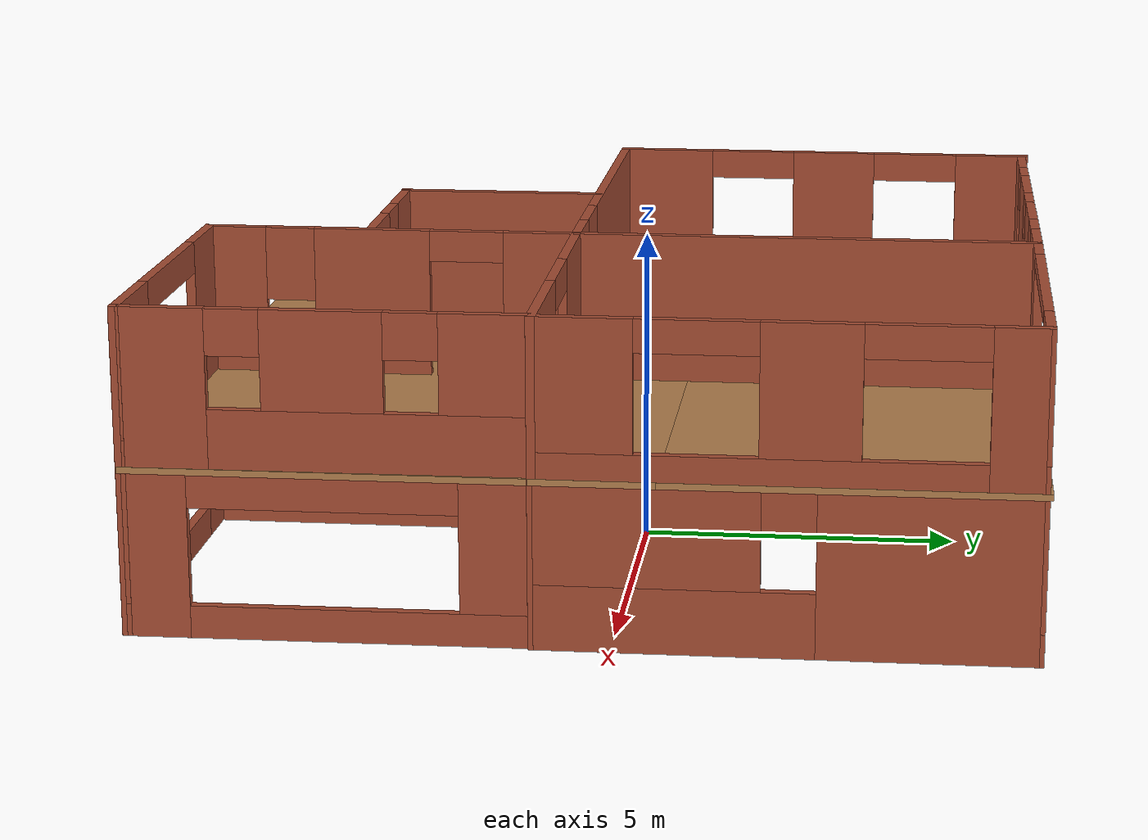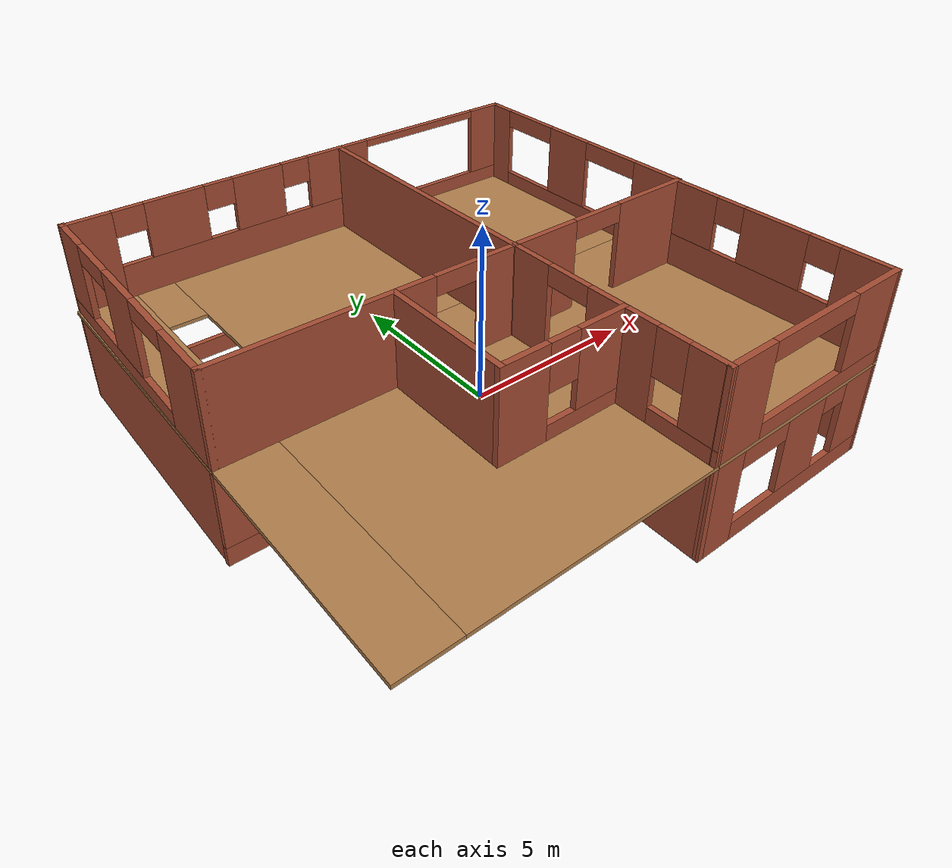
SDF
<?xml version='1.0'?>
<sdf version='1.6'>
  <model name='HouseTwoLevels'>
    <pose frame=''>-1.03567 -0.470569 0 0 -0 0</pose>
    <link name='Floor_0'>
      <pose frame=''>0 8.2e-05 2.5 0 -0 0</pose>
      <visual name='Floor_0_Visual_0'>
        <pose frame=''>-6.0357 0 0.05 0 -0 0</pose>
        <geometry>
          <box>
            <size>1.47202 13.5434 0.1</size>
          </box>
        </geometry>
        <material>
          <script>
            <uri>file://media/materials/scripts/gazebo.material</uri>
            <name>Gazebo/Wood</name>
          </script>
          <ambient>1 1 1 1</ambient>
        </material>
      </visual>
      <collision name='Floor_0_Collision_0'>
        <geometry>
          <box>
            <size>1.47202 13.5434 0.1</size>
          </box>
        </geometry>
        <pose frame=''>-6.0357 0 0.05 0 -0 0</pose>
      </collision>
      <visual name='Floor_0_Visual_1'>
        <pose frame=''>0.736013 -2.82095 0.05 0 -0 0</pose>
        <geometry>
          <box>
            <size>12.0714 7.90153 0.1</size>
          </box>
        </geometry>
        <material>
          <script>
            <uri>file://media/materials/scripts/gazebo.material</uri>
            <name>Gazebo/Wood</name>
          </script>
          <ambient>1 1 1 1</ambient>
        </material>
      </visual>
      <collision name='Floor_0_Collision_1'>
        <geometry>
          <box>
            <size>12.0714 7.90153 0.1</size>
          </box>
        </geometry>
        <pose frame=''>0.736013 -2.82095 0.05 0 -0 0</pose>
      </collision>
      <visual name='Floor_0_Visual_2'>
        <pose frame=''>1.23601 3.95076 0.05 0 -0 0</pose>
        <geometry>
          <box>
            <size>11.0714 5.6419 0.1</size>
          </box>
        </geometry>
        <material>
          <script>
            <uri>file://media/materials/scripts/gazebo.material</uri>
            <name>Gazebo/Wood</name>
          </script>
          <ambient>1 1 1 1</ambient>
        </material>
      </visual>
      <collision name='Floor_0_Collision_2'>
        <geometry>
          <box>
            <size>11.0714 5.6419 0.1</size>
          </box>
        </geometry>
        <pose frame=''>1.23601 3.95076 0.05 0 -0 0</pose>
      </collision>
      <visual name='Floor_0_Visual_3'>
        <pose frame=''>-4.79969 5.70076 0.05 0 -0 0</pose>
        <geometry>
          <box>
            <size>1 2.1419 0.1</size>
          </box>
        </geometry>
        <material>
          <script>
            <uri>file://media/materials/scripts/gazebo.material</uri>
            <name>Gazebo/Wood</name>
          </script>
          <ambient>1 1 1 1</ambient>
        </material>
      </visual>
      <collision name='Floor_0_Collision_3'>
        <geometry>
          <box>
            <size>1 2.1419 0.1</size>
          </box>
        </geometry>
        <pose frame=''>-4.79969 5.70076 0.05 0 -0 0</pose>
      </collision>
    </link>
    <link name='Stairs_0'>
      <visual name='Stairs_0_Visual_0'>
        <pose frame=''>-4.79969 4.51323 0.083333 0 -0 0</pose>
        <geometry>
          <box>
            <size>1 0.233333 0.166667</size>
          </box>
        </geometry>
        <material>
          <script>
            <uri>file://media/materials/scripts/gazebo.material</uri>
            <name>Gazebo/Grey</name>
          </script>
          <ambient>1 1 1 1</ambient>
        </material>
      </visual>
      <collision name='Stairs_0_Collision_0'>
        <geometry>
          <box>
            <size>1 0.233333 0.166667</size>
          </box>
        </geometry>
        <pose frame=''>-4.79969 4.51323 0.083333 0 -0 0</pose>
      </collision>
      <visual name='Stairs_0_Visual_1'>
        <pose frame=''>-4.79969 4.2799 0.25 0 -0 0</pose>
        <geometry>
          <box>
            <size>1 0.233333 0.166667</size>
          </box>
        </geometry>
        <material>
          <script>
            <uri>file://media/materials/scripts/gazebo.material</uri>
            <name>Gazebo/Grey</name>
          </script>
          <ambient>1 1 1 1</ambient>
        </material>
      </visual>
      <collision name='Stairs_0_Collision_1'>
        <geometry>
          <box>
            <size>1 0.233333 0.166667</size>
          </box>
        </geometry>
        <pose frame=''>-4.79969 4.2799 0.25 0 -0 0</pose>
      </collision>
      <visual name='Stairs_0_Visual_2'>
        <pose frame=''>-4.79969 4.04656 0.416667 0 -0 0</pose>
        <geometry>
          <box>
            <size>1 0.233333 0.166667</size>
          </box>
        </geometry>
        <material>
          <script>
            <uri>file://media/materials/scripts/gazebo.material</uri>
            <name>Gazebo/Grey</name>
          </script>
          <ambient>1 1 1 1</ambient>
        </material>
      </visual>
      <collision name='Stairs_0_Collision_2'>
        <geometry>
          <box>
            <size>1 0.233333 0.166667</size>
          </box>
        </geometry>
        <pose frame=''>-4.79969 4.04656 0.416667 0 -0 0</pose>
      </collision>
      <visual name='Stairs_0_Visual_3'>
        <pose frame=''>-4.79969 3.81323 0.583333 0 -0 0</pose>
        <geometry>
          <box>
            <size>1 0.233333 0.166667</size>
          </box>
        </geometry>
        <material>
          <script>
            <uri>file://media/materials/scripts/gazebo.material</uri>
            <name>Gazebo/Grey</name>
          </script>
          <ambient>1 1 1 1</ambient>
        </material>
      </visual>
      <collision name='Stairs_0_Collision_3'>
        <geometry>
          <box>
            <size>1 0.233333 0.166667</size>
          </box>
        </geometry>
        <pose frame=''>-4.79969 3.81323 0.583333 0 -0 0</pose>
      </collision>
      <visual name='Stairs_0_Visual_4'>
        <pose frame=''>-4.79969 3.5799 0.75 0 -0 0</pose>
        <geometry>
          <box>
            <size>1 0.233333 0.166667</size>
          </box>
        </geometry>
        <material>
          <script>
            <uri>file://media/materials/scripts/gazebo.material</uri>
            <name>Gazebo/Grey</name>
          </script>
          <ambient>1 1 1 1</ambient>
        </material>
      </visual>
      <collision name='Stairs_0_Collision_4'>
        <geometry>
          <box>
            <size>1 0.233333 0.166667</size>
          </box>
        </geometry>
        <pose frame=''>-4.79969 3.5799 0.75 0 -0 0</pose>
      </collision>
      <visual name='Stairs_0_Visual_5'>
        <pose frame=''>-4.79969 3.34656 0.916667 0 -0 0</pose>
        <geometry>
          <box>
            <size>1 0.233333 0.166667</size>
          </box>
        </geometry>
        <material>
          <script>
            <uri>file://media/materials/scripts/gazebo.material</uri>
            <name>Gazebo/Grey</name>
          </script>
          <ambient>1 1 1 1</ambient>
        </material>
      </visual>
      <collision name='Stairs_0_Collision_5'>
        <geometry>
          <box>
            <size>1 0.233333 0.166667</size>
          </box>
        </geometry>
        <pose frame=''>-4.79969 3.34656 0.916667 0 -0 0</pose>
      </collision>
      <visual name='Stairs_0_Visual_6'>
        <pose frame=''>-4.79969 3.11323 1.08333 0 -0 0</pose>
        <geometry>
          <box>
            <size>1 0.233333 0.166667</size>
          </box>
        </geometry>
        <material>
          <script>
            <uri>file://media/materials/scripts/gazebo.material</uri>
            <name>Gazebo/Grey</name>
          </script>
          <ambient>1 1 1 1</ambient>
        </material>
      </visual>
      <collision name='Stairs_0_Collision_6'>
        <geometry>
          <box>
            <size>1 0.233333 0.166667</size>
          </box>
        </geometry>
        <pose frame=''>-4.79969 3.11323 1.08333 0 -0 0</pose>
      </collision>
      <visual name='Stairs_0_Visual_7'>
        <pose frame=''>-4.79969 2.87989 1.25 0 -0 0</pose>
        <geometry>
          <box>
            <size>1 0.233333 0.166667</size>
          </box>
        </geometry>
        <material>
          <script>
            <uri>file://media/materials/scripts/gazebo.material</uri>
            <name>Gazebo/Grey</name>
          </script>
          <ambient>1 1 1 1</ambient>
        </material>
      </visual>
      <collision name='Stairs_0_Collision_7'>
        <geometry>
          <box>
            <size>1 0.233333 0.166667</size>
          </box>
        </geometry>
        <pose frame=''>-4.79969 2.87989 1.25 0 -0 0</pose>
      </collision>
      <visual name='Stairs_0_Visual_8'>
        <pose frame=''>-4.79969 2.64656 1.41667 0 -0 0</pose>
        <geometry>
          <box>
            <size>1 0.233333 0.166667</size>
          </box>
        </geometry>
        <material>
          <script>
            <uri>file://media/materials/scripts/gazebo.material</uri>
            <name>Gazebo/Grey</name>
          </script>
          <ambient>1 1 1 1</ambient>
        </material>
      </visual>
      <collision name='Stairs_0_Collision_8'>
        <geometry>
          <box>
            <size>1 0.233333 0.166667</size>
          </box>
        </geometry>
        <pose frame=''>-4.79969 2.64656 1.41667 0 -0 0</pose>
      </collision>
      <visual name='Stairs_0_Visual_9'>
        <pose frame=''>-4.79969 2.41323 1.58333 0 -0 0</pose>
        <geometry>
          <box>
            <size>1 0.233333 0.166667</size>
          </box>
        </geometry>
        <material>
          <script>
            <uri>file://media/materials/scripts/gazebo.material</uri>
            <name>Gazebo/Grey</name>
          </script>
          <ambient>1 1 1 1</ambient>
        </material>
      </visual>
      <collision name='Stairs_0_Collision_9'>
        <geometry>
          <box>
            <size>1 0.233333 0.166667</size>
          </box>
        </geometry>
        <pose frame=''>-4.79969 2.41323 1.58333 0 -0 0</pose>
      </collision>
      <visual name='Stairs_0_Visual_10'>
        <pose frame=''>-4.79969 2.1799 1.75 0 -0 0</pose>
        <geometry>
          <box>
            <size>1 0.233333 0.166667</size>
          </box>
        </geometry>
        <material>
          <script>
            <uri>file://media/materials/scripts/gazebo.material</uri>
            <name>Gazebo/Grey</name>
          </script>
          <ambient>1 1 1 1</ambient>
        </material>
      </visual>
      <collision name='Stairs_0_Collision_10'>
        <geometry>
          <box>
            <size>1 0.233333 0.166667</size>
          </box>
        </geometry>
        <pose frame=''>-4.79969 2.1799 1.75 0 -0 0</pose>
      </collision>
      <visual name='Stairs_0_Visual_11'>
        <pose frame=''>-4.79969 1.94656 1.91667 0 -0 0</pose>
        <geometry>
          <box>
            <size>1 0.233333 0.166667</size>
          </box>
        </geometry>
        <material>
          <script>
            <uri>file://media/materials/scripts/gazebo.material</uri>
            <name>Gazebo/Grey</name>
          </script>
          <ambient>1 1 1 1</ambient>
        </material>
      </visual>
      <collision name='Stairs_0_Collision_11'>
        <geometry>
          <box>
            <size>1 0.233333 0.166667</size>
          </box>
        </geometry>
        <pose frame=''>-4.79969 1.94656 1.91667 0 -0 0</pose>
      </collision>
      <visual name='Stairs_0_Visual_12'>
        <pose frame=''>-4.79969 1.71323 2.08333 0 -0 0</pose>
        <geometry>
          <box>
            <size>1 0.233333 0.166667</size>
          </box>
        </geometry>
        <material>
          <script>
            <uri>file://media/materials/scripts/gazebo.material</uri>
            <name>Gazebo/Grey</name>
          </script>
          <ambient>1 1 1 1</ambient>
        </material>
      </visual>
      <collision name='Stairs_0_Collision_12'>
        <geometry>
          <box>
            <size>1 0.233333 0.166667</size>
          </box>
        </geometry>
        <pose frame=''>-4.79969 1.71323 2.08333 0 -0 0</pose>
      </collision>
      <visual name='Stairs_0_Visual_13'>
        <pose frame=''>-4.79969 1.47989 2.25 0 -0 0</pose>
        <geometry>
          <box>
            <size>1 0.233333 0.166667</size>
          </box>
        </geometry>
        <material>
          <script>
            <uri>file://media/materials/scripts/gazebo.material</uri>
            <name>Gazebo/Grey</name>
          </script>
          <ambient>1 1 1 1</ambient>
        </material>
      </visual>
      <collision name='Stairs_0_Collision_13'>
        <geometry>
          <box>
            <size>1 0.233333 0.166667</size>
          </box>
        </geometry>
        <pose frame=''>-4.79969 1.47989 2.25 0 -0 0</pose>
      </collision>
      <visual name='Stairs_0_Visual_14'>
        <pose frame=''>-4.79969 1.24656 2.41667 0 -0 0</pose>
        <geometry>
          <box>
            <size>1 0.233333 0.166667</size>
          </box>
        </geometry>
        <material>
          <script>
            <uri>file://media/materials/scripts/gazebo.material</uri>
            <name>Gazebo/Grey</name>
          </script>
          <ambient>1 1 1 1</ambient>
        </material>
      </visual>
      <collision name='Stairs_0_Collision_14'>
        <geometry>
          <box>
            <size>1 0.233333 0.166667</size>
          </box>
        </geometry>
        <pose frame=''>-4.79969 1.24656 2.41667 0 -0 0</pose>
      </collision>
    </link>
    <link name='Wall_1'>
      <pose frame=''>-2.82202 6.66175 0 0 -0 0.003021</pose>
      <visual name='Wall_1_Visual_0'>
        <pose frame=''>-3.08451 0 1.25 0 -0 0</pose>
        <geometry>
          <box>
            <size>1.63724 0.15 2.5</size>
          </box>
        </geometry>
        <material>
          <script>
            <uri>file://media/materials/scripts/gazebo.material</uri>
            <name>Gazebo/Bricks</name>
          </script>
          <ambient>1 1 1 1</ambient>
        </material>
      </visual>
      <collision name='Wall_1_Collision_0'>
        <geometry>
          <box>
            <size>1.63724 0.15 2.5</size>
          </box>
        </geometry>
        <pose frame=''>-3.08451 0 1.25 0 -0 0</pose>
      </collision>
      <visual name='Wall_1_Visual_1'>
        <pose frame=''>0.818619 0 0.25 0 -0 0</pose>
        <geometry>
          <box>
            <size>6.16903 0.15 0.5</size>
          </box>
        </geometry>
        <material>
          <script>
            <uri>file://media/materials/scripts/gazebo.material</uri>
            <name>Gazebo/Bricks</name>
          </script>
          <ambient>1 1 1 1</ambient>
        </material>
      </visual>
      <collision name='Wall_1_Collision_1'>
        <geometry>
          <box>
            <size>6.16903 0.15 0.5</size>
          </box>
        </geometry>
        <pose frame=''>0.818619 0 0.25 0 -0 0</pose>
      </collision>
      <visual name='Wall_1_Visual_2'>
        <pose frame=''>2.81862 0 1.5 0 -0 0</pose>
        <geometry>
          <box>
            <size>2.16903 0.15 2</size>
          </box>
        </geometry>
        <material>
          <script>
            <uri>file://media/materials/scripts/gazebo.material</uri>
            <name>Gazebo/Bricks</name>
          </script>
          <ambient>1 1 1 1</ambient>
        </material>
      </visual>
      <collision name='Wall_1_Collision_2'>
        <geometry>
          <box>
            <size>2.16903 0.15 2</size>
          </box>
        </geometry>
        <pose frame=''>2.81862 0 1.5 0 -0 0</pose>
      </collision>
      <visual name='Wall_1_Visual_3'>
        <pose frame=''>-0.265896 0 2.4 0 -0 0</pose>
        <geometry>
          <box>
            <size>4 0.15 0.2</size>
          </box>
        </geometry>
        <material>
          <script>
            <uri>file://media/materials/scripts/gazebo.material</uri>
            <name>Gazebo/Bricks</name>
          </script>
          <ambient>1 1 1 1</ambient>
        </material>
      </visual>
      <collision name='Wall_1_Collision_3'>
        <geometry>
          <box>
            <size>4 0.15 0.2</size>
          </box>
        </geometry>
        <pose frame=''>-0.265896 0 2.4 0 -0 0</pose>
      </collision>
    </link>
    <link name='Wall_10'>
      <pose frame=''>3.85116 -6.69618 0 0 -0 0</pose>
      <visual name='Wall_10_Visual_0'>
        <pose frame=''>-2.4133 0 1.25 0 -0 0</pose>
        <geometry>
          <box>
            <size>1.01353 0.15 2.5</size>
          </box>
        </geometry>
        <material>
          <script>
            <uri>file://media/materials/scripts/gazebo.material</uri>
            <name>Gazebo/Bricks</name>
          </script>
          <ambient>1 1 1 1</ambient>
        </material>
      </visual>
      <collision name='Wall_10_Collision_0'>
        <geometry>
          <box>
            <size>1.01353 0.15 2.5</size>
          </box>
        </geometry>
        <pose frame=''>-2.4133 0 1.25 0 -0 0</pose>
      </collision>
      <visual name='Wall_10_Visual_1'>
        <pose frame=''>0.506767 0 0.25 0 -0 0</pose>
        <geometry>
          <box>
            <size>4.8266 0.15 0.5</size>
          </box>
        </geometry>
        <material>
          <script>
            <uri>file://media/materials/scripts/gazebo.material</uri>
            <name>Gazebo/Bricks</name>
          </script>
          <ambient>1 1 1 1</ambient>
        </material>
      </visual>
      <collision name='Wall_10_Collision_1'>
        <geometry>
          <box>
            <size>4.8266 0.15 0.5</size>
          </box>
        </geometry>
        <pose frame=''>0.506767 0 0.25 0 -0 0</pose>
      </collision>
      <visual name='Wall_10_Visual_2'>
        <pose frame=''>0.267522 0 1.5 0 -0 0</pose>
        <geometry>
          <box>
            <size>1.34811 0.15 2</size>
          </box>
        </geometry>
        <material>
          <script>
            <uri>file://media/materials/scripts/gazebo.material</uri>
            <name>Gazebo/Bricks</name>
          </script>
          <ambient>1 1 1 1</ambient>
        </material>
      </visual>
      <collision name='Wall_10_Collision_2'>
        <geometry>
          <box>
            <size>1.34811 0.15 2</size>
          </box>
        </geometry>
        <pose frame=''>0.267522 0 1.5 0 -0 0</pose>
      </collision>
      <visual name='Wall_10_Visual_3'>
        <pose frame=''>2.33082 0 1.5 0 -0 0</pose>
        <geometry>
          <box>
            <size>1.17849 0.15 2</size>
          </box>
        </geometry>
        <material>
          <script>
            <uri>file://media/materials/scripts/gazebo.material</uri>
            <name>Gazebo/Bricks</name>
          </script>
          <ambient>1 1 1 1</ambient>
        </material>
      </visual>
      <collision name='Wall_10_Collision_3'>
        <geometry>
          <box>
            <size>1.17849 0.15 2</size>
          </box>
        </geometry>
        <pose frame=''>2.33082 0 1.5 0 -0 0</pose>
      </collision>
      <visual name='Wall_10_Visual_4'>
        <pose frame=''>-1.15653 0 2.25 0 -0 0</pose>
        <geometry>
          <box>
            <size>1.5 0.15 0.5</size>
          </box>
        </geometry>
        <material>
          <script>
            <uri>file://media/materials/scripts/gazebo.material</uri>
            <name>Gazebo/Bricks</name>
          </script>
          <ambient>1 1 1 1</ambient>
        </material>
      </visual>
      <collision name='Wall_10_Collision_4'>
        <geometry>
          <box>
            <size>1.5 0.15 0.5</size>
          </box>
        </geometry>
        <pose frame=''>-1.15653 0 2.25 0 -0 0</pose>
      </collision>
      <visual name='Wall_10_Visual_5'>
        <pose frame=''>1.34157 0 2.25 0 -0 0</pose>
        <geometry>
          <box>
            <size>0.8 0.15 0.5</size>
          </box>
        </geometry>
        <material>
          <script>
            <uri>file://media/materials/scripts/gazebo.material</uri>
            <name>Gazebo/Bricks</name>
          </script>
          <ambient>1 1 1 1</ambient>
        </material>
      </visual>
      <collision name='Wall_10_Collision_5'>
        <geometry>
          <box>
            <size>0.8 0.15 0.5</size>
          </box>
        </geometry>
        <pose frame=''>1.34157 0 2.25 0 -0 0</pose>
      </collision>
    </link>
    <link name='Wall_11'>
      <pose frame=''>6.6731 -3.6892 0 0 -0 1.57849</pose>
      <visual name='Wall_11_Visual_0'>
        <pose frame=''>-2.56461 0 1.25 0 -0 0</pose>
        <geometry>
          <box>
            <size>1.03492 0.15 2.5</size>
          </box>
        </geometry>
        <material>
          <script>
            <uri>file://media/materials/scripts/gazebo.material</uri>
            <name>Gazebo/Bricks</name>
          </script>
          <ambient>1 1 1 1</ambient>
        </material>
      </visual>
      <collision name='Wall_11_Collision_0'>
        <geometry>
          <box>
            <size>1.03492 0.15 2.5</size>
          </box>
        </geometry>
        <pose frame=''>-2.56461 0 1.25 0 -0 0</pose>
      </collision>
      <visual name='Wall_11_Visual_1'>
        <pose frame=''>0.517459 0 0.25 0 -0 0</pose>
        <geometry>
          <box>
            <size>5.12922 0.15 0.5</size>
          </box>
        </geometry>
        <material>
          <script>
            <uri>file://media/materials/scripts/gazebo.material</uri>
            <name>Gazebo/Bricks</name>
          </script>
          <ambient>1 1 1 1</ambient>
        </material>
      </visual>
      <collision name='Wall_11_Collision_1'>
        <geometry>
          <box>
            <size>5.12922 0.15 0.5</size>
          </box>
        </geometry>
        <pose frame=''>0.517459 0 0.25 0 -0 0</pose>
      </collision>
      <visual name='Wall_11_Visual_2'>
        <pose frame=''>2.51746 0 1.5 0 -0 0</pose>
        <geometry>
          <box>
            <size>1.12922 0.15 2</size>
          </box>
        </geometry>
        <material>
          <script>
            <uri>file://media/materials/scripts/gazebo.material</uri>
            <name>Gazebo/Bricks</name>
          </script>
          <ambient>1 1 1 1</ambient>
        </material>
      </visual>
      <collision name='Wall_11_Collision_2'>
        <geometry>
          <box>
            <size>1.12922 0.15 2</size>
          </box>
        </geometry>
        <pose frame=''>2.51746 0 1.5 0 -0 0</pose>
      </collision>
      <visual name='Wall_11_Visual_3'>
        <pose frame=''>-0.04715 0 2.25 0 -0 0</pose>
        <geometry>
          <box>
            <size>4 0.15 0.5</size>
          </box>
        </geometry>
        <material>
          <script>
            <uri>file://media/materials/scripts/gazebo.material</uri>
            <name>Gazebo/Bricks</name>
          </script>
          <ambient>1 1 1 1</ambient>
        </material>
      </visual>
      <collision name='Wall_11_Collision_3'>
        <geometry>
          <box>
            <size>4 0.15 0.5</size>
          </box>
        </geometry>
        <pose frame=''>-0.04715 0 2.25 0 -0 0</pose>
      </collision>
    </link>
    <link name='Wall_13'>
      <pose frame=''>-2.31315 0.867533 0 0 -0 1.56333</pose>
      <visual name='Wall_13_Visual_0'>
        <pose frame=''>-1.17001 0 1.25 0 -0 0</pose>
        <geometry>
          <box>
            <size>0.909576 0.15 2.5</size>
          </box>
        </geometry>
        <material>
          <script>
            <uri>file://media/materials/scripts/gazebo.material</uri>
            <name>Gazebo/Bricks</name>
          </script>
          <ambient>1 1 1 1</ambient>
        </material>
      </visual>
      <collision name='Wall_13_Collision_0'>
        <geometry>
          <box>
            <size>0.909576 0.15 2.5</size>
          </box>
        </geometry>
        <pose frame=''>-1.17001 0 1.25 0 -0 0</pose>
      </collision>
      <visual name='Wall_13_Visual_1'>
        <pose frame=''>1.05479 0 1.25 0 -0 0</pose>
        <geometry>
          <box>
            <size>1.14001 0.15 2.5</size>
          </box>
        </geometry>
        <material>
          <script>
            <uri>file://media/materials/scripts/gazebo.material</uri>
            <name>Gazebo/Bricks</name>
          </script>
          <ambient>1 1 1 1</ambient>
        </material>
      </visual>
      <collision name='Wall_13_Collision_1'>
        <geometry>
          <box>
            <size>1.14001 0.15 2.5</size>
          </box>
        </geometry>
        <pose frame=''>1.05479 0 1.25 0 -0 0</pose>
      </collision>
      <visual name='Wall_13_Visual_2'>
        <pose frame=''>-0.115218 0 2.25 0 -0 0</pose>
        <geometry>
          <box>
            <size>1.2 0.15 0.5</size>
          </box>
        </geometry>
        <material>
          <script>
            <uri>file://media/materials/scripts/gazebo.material</uri>
            <name>Gazebo/Bricks</name>
          </script>
          <ambient>1 1 1 1</ambient>
        </material>
      </visual>
      <collision name='Wall_13_Collision_2'>
        <geometry>
          <box>
            <size>1.2 0.15 0.5</size>
          </box>
        </geometry>
        <pose frame=''>-0.115218 0 2.25 0 -0 0</pose>
      </collision>
    </link>
    <link name='Wall_15'>
      <collision name='Wall_15_Collision'>
        <geometry>
          <box>
            <size>3.45768 0.15 2.5</size>
          </box>
        </geometry>
        <pose frame=''>0 0 1.25 0 -0 0</pose>
      </collision>
      <visual name='Wall_15_Visual'>
        <pose frame=''>0 0 1.25 0 -0 0</pose>
        <geometry>
          <box>
            <size>3.45768 0.15 2.5</size>
          </box>
        </geometry>
        <material>
          <script>
            <uri>file://media/materials/scripts/gazebo.material</uri>
            <name>Gazebo/Bricks</name>
          </script>
          <ambient>1 1 1 1</ambient>
        </material>
      </visual>
      <pose frame=''>-0.647741 2.34789 0 0 -0 0</pose>
    </link>
    <link name='Wall_17'>
      <collision name='Wall_17_Collision'>
        <geometry>
          <box>
            <size>3.48113 0.15 2.5</size>
          </box>
        </geometry>
        <pose frame=''>0 0 1.25 0 -0 0</pose>
      </collision>
      <visual name='Wall_17_Visual'>
        <pose frame=''>0 0 1.25 0 -0 0</pose>
        <geometry>
          <box>
            <size>3.48113 0.15 2.5</size>
          </box>
        </geometry>
        <material>
          <script>
            <uri>file://media/materials/scripts/gazebo.material</uri>
            <name>Gazebo/Bricks</name>
          </script>
          <ambient>1 1 1 1</ambient>
        </material>
      </visual>
      <pose frame=''>-2.30158 -2.37075 0 0 0 -1.5708</pose>
    </link>
    <link name='Wall_18'>
      <pose frame=''>-0.647741 -4.03616 0 0 -0 0</pose>
      <visual name='Wall_18_Visual_0'>
        <pose frame=''>-1.33772 0 1.25 0 -0 0</pose>
        <geometry>
          <box>
            <size>0.782228 0.15 2.5</size>
          </box>
        </geometry>
        <material>
          <script>
            <uri>file://media/materials/scripts/gazebo.material</uri>
            <name>Gazebo/Bricks</name>
          </script>
          <ambient>1 1 1 1</ambient>
        </material>
      </visual>
      <collision name='Wall_18_Collision_0'>
        <geometry>
          <box>
            <size>0.782228 0.15 2.5</size>
          </box>
        </geometry>
        <pose frame=''>-1.33772 0 1.25 0 -0 0</pose>
      </collision>
      <visual name='Wall_18_Visual_1'>
        <pose frame=''>1.14111 0 1.25 0 -0 0</pose>
        <geometry>
          <box>
            <size>1.17545 0.15 2.5</size>
          </box>
        </geometry>
        <material>
          <script>
            <uri>file://media/materials/scripts/gazebo.material</uri>
            <name>Gazebo/Bricks</name>
          </script>
          <ambient>1 1 1 1</ambient>
        </material>
      </visual>
      <collision name='Wall_18_Collision_1'>
        <geometry>
          <box>
            <size>1.17545 0.15 2.5</size>
          </box>
        </geometry>
        <pose frame=''>1.14111 0 1.25 0 -0 0</pose>
      </collision>
      <visual name='Wall_18_Visual_2'>
        <pose frame=''>-0.19661 0 2.25 0 -0 0</pose>
        <geometry>
          <box>
            <size>1.5 0.15 0.5</size>
          </box>
        </geometry>
        <material>
          <script>
            <uri>file://media/materials/scripts/gazebo.material</uri>
            <name>Gazebo/Bricks</name>
          </script>
          <ambient>1 1 1 1</ambient>
        </material>
      </visual>
      <collision name='Wall_18_Collision_2'>
        <geometry>
          <box>
            <size>1.5 0.15 0.5</size>
          </box>
        </geometry>
        <pose frame=''>-0.19661 0 2.25 0 -0 0</pose>
      </collision>
    </link>
    <link name='Wall_2'>
      <pose frame=''>1.01766 2.99555 0 0 0 -1.56765</pose>
      <visual name='Wall_2_Visual_0'>
        <pose frame=''>-1.12434 0 1.25 0 -0 0</pose>
        <geometry>
          <box>
            <size>5.2569 0.15 2.5</size>
          </box>
        </geometry>
        <material>
          <script>
            <uri>file://media/materials/scripts/gazebo.material</uri>
            <name>Gazebo/Bricks</name>
          </script>
          <ambient>1 1 1 1</ambient>
        </material>
      </visual>
      <collision name='Wall_2_Collision_0'>
        <geometry>
          <box>
            <size>5.2569 0.15 2.5</size>
          </box>
        </geometry>
        <pose frame=''>-1.12434 0 1.25 0 -0 0</pose>
      </collision>
      <visual name='Wall_2_Visual_1'>
        <pose frame=''>3.22845 0 1.25 0 -0 0</pose>
        <geometry>
          <box>
            <size>1.04867 0.15 2.5</size>
          </box>
        </geometry>
        <material>
          <script>
            <uri>file://media/materials/scripts/gazebo.material</uri>
            <name>Gazebo/Bricks</name>
          </script>
          <ambient>1 1 1 1</ambient>
        </material>
      </visual>
      <collision name='Wall_2_Collision_1'>
        <geometry>
          <box>
            <size>1.04867 0.15 2.5</size>
          </box>
        </geometry>
        <pose frame=''>3.22845 0 1.25 0 -0 0</pose>
      </collision>
      <visual name='Wall_2_Visual_2'>
        <pose frame=''>2.10411 0 2.25 0 -0 0</pose>
        <geometry>
          <box>
            <size>1.2 0.15 0.5</size>
          </box>
        </geometry>
        <material>
          <script>
            <uri>file://media/materials/scripts/gazebo.material</uri>
            <name>Gazebo/Bricks</name>
          </script>
          <ambient>1 1 1 1</ambient>
        </material>
      </visual>
      <collision name='Wall_2_Collision_2'>
        <geometry>
          <box>
            <size>1.2 0.15 0.5</size>
          </box>
        </geometry>
        <pose frame=''>2.10411 0 2.25 0 -0 0</pose>
      </collision>
    </link>
    <link name='Wall_20'>
      <pose frame=''>-2.82202 6.66175 2.5 0 -0 0.003021</pose>
      <visual name='Wall_20_Visual_0'>
        <pose frame=''>-3.29062 0 1.25 0 -0 0</pose>
        <geometry>
          <box>
            <size>1.22502 0.15 2.5</size>
          </box>
        </geometry>
        <material>
          <script>
            <uri>file://media/materials/scripts/gazebo.material</uri>
            <name>Gazebo/Bricks</name>
          </script>
          <ambient>1 1 1 1</ambient>
        </material>
      </visual>
      <collision name='Wall_20_Collision_0'>
        <geometry>
          <box>
            <size>1.22502 0.15 2.5</size>
          </box>
        </geometry>
        <pose frame=''>-3.29062 0 1.25 0 -0 0</pose>
      </collision>
      <visual name='Wall_20_Visual_1'>
        <pose frame=''>0.612511 0 0.5 0 -0 0</pose>
        <geometry>
          <box>
            <size>6.58124 0.15 1</size>
          </box>
        </geometry>
        <material>
          <script>
            <uri>file://media/materials/scripts/gazebo.material</uri>
            <name>Gazebo/Bricks</name>
          </script>
          <ambient>1 1 1 1</ambient>
        </material>
      </visual>
      <collision name='Wall_20_Collision_1'>
        <geometry>
          <box>
            <size>6.58124 0.15 1</size>
          </box>
        </geometry>
        <pose frame=''>0.612511 0 0.5 0 -0 0</pose>
      </collision>
      <visual name='Wall_20_Visual_2'>
        <pose frame=''>-1.0755 0 1.75 0 -0 0</pose>
        <geometry>
          <box>
            <size>1.60522 0.15 1.5</size>
          </box>
        </geometry>
        <material>
          <script>
            <uri>file://media/materials/scripts/gazebo.material</uri>
            <name>Gazebo/Bricks</name>
          </script>
          <ambient>1 1 1 1</ambient>
        </material>
      </visual>
      <collision name='Wall_20_Collision_2'>
        <geometry>
          <box>
            <size>1.60522 0.15 1.5</size>
          </box>
        </geometry>
        <pose frame=''>-1.0755 0 1.75 0 -0 0</pose>
      </collision>
      <visual name='Wall_20_Visual_3'>
        <pose frame=''>1.24922 0 1.75 0 -0 0</pose>
        <geometry>
          <box>
            <size>1.44422 0.15 1.5</size>
          </box>
        </geometry>
        <material>
          <script>
            <uri>file://media/materials/scripts/gazebo.material</uri>
            <name>Gazebo/Bricks</name>
          </script>
          <ambient>1 1 1 1</ambient>
        </material>
      </visual>
      <collision name='Wall_20_Collision_3'>
        <geometry>
          <box>
            <size>1.44422 0.15 1.5</size>
          </box>
        </geometry>
        <pose frame=''>1.24922 0 1.75 0 -0 0</pose>
      </collision>
      <visual name='Wall_20_Visual_4'>
        <pose frame=''>3.33723 0 1.75 0 -0 0</pose>
        <geometry>
          <box>
            <size>1.1318 0.15 1.5</size>
          </box>
        </geometry>
        <material>
          <script>
            <uri>file://media/materials/scripts/gazebo.material</uri>
            <name>Gazebo/Bricks</name>
          </script>
          <ambient>1 1 1 1</ambient>
        </material>
      </visual>
      <collision name='Wall_20_Collision_4'>
        <geometry>
          <box>
            <size>1.1318 0.15 1.5</size>
          </box>
        </geometry>
        <pose frame=''>3.33723 0 1.75 0 -0 0</pose>
      </collision>
      <visual name='Wall_20_Visual_5'>
        <pose frame=''>-2.27811 0 2.15 0 -0 0</pose>
        <geometry>
          <box>
            <size>0.8 0.15 0.7</size>
          </box>
        </geometry>
        <material>
          <script>
            <uri>file://media/materials/scripts/gazebo.material</uri>
            <name>Gazebo/Bricks</name>
          </script>
          <ambient>1 1 1 1</ambient>
        </material>
      </visual>
      <collision name='Wall_20_Collision_5'>
        <geometry>
          <box>
            <size>0.8 0.15 0.7</size>
          </box>
        </geometry>
        <pose frame=''>-2.27811 0 2.15 0 -0 0</pose>
      </collision>
      <visual name='Wall_20_Visual_6'>
        <pose frame=''>0.127113 0 2.15 0 -0 0</pose>
        <geometry>
          <box>
            <size>0.8 0.15 0.7</size>
          </box>
        </geometry>
        <material>
          <script>
            <uri>file://media/materials/scripts/gazebo.material</uri>
            <name>Gazebo/Bricks</name>
          </script>
          <ambient>1 1 1 1</ambient>
        </material>
      </visual>
      <collision name='Wall_20_Collision_6'>
        <geometry>
          <box>
            <size>0.8 0.15 0.7</size>
          </box>
        </geometry>
        <pose frame=''>0.127113 0 2.15 0 -0 0</pose>
      </collision>
      <visual name='Wall_20_Visual_7'>
        <pose frame=''>2.37133 0 2.15 0 -0 0</pose>
        <geometry>
          <box>
            <size>0.8 0.15 0.7</size>
          </box>
        </geometry>
        <material>
          <script>
            <uri>file://media/materials/scripts/gazebo.material</uri>
            <name>Gazebo/Bricks</name>
          </script>
          <ambient>1 1 1 1</ambient>
        </material>
      </visual>
      <collision name='Wall_20_Collision_7'>
        <geometry>
          <box>
            <size>0.8 0.15 0.7</size>
          </box>
        </geometry>
        <pose frame=''>2.37133 0 2.15 0 -0 0</pose>
      </collision>
    </link>
    <link name='Wall_21'>
      <collision name='Wall_21_Collision'>
        <geometry>
          <box>
            <size>7.50557 0.15 2.5</size>
          </box>
        </geometry>
        <pose frame=''>0 0 1.25 0 -0 0</pose>
      </collision>
      <visual name='Wall_21_Visual'>
        <pose frame=''>0 0 1.25 0 -0 0</pose>
        <geometry>
          <box>
            <size>7.50557 0.15 2.5</size>
          </box>
        </geometry>
        <material>
          <script>
            <uri>file://media/materials/scripts/gazebo.material</uri>
            <name>Gazebo/Bricks</name>
          </script>
          <ambient>1 1 1 1</ambient>
        </material>
      </visual>
      <pose frame=''>1.00588 2.99544 2.5 0 0 -1.57085</pose>
    </link>
    <link name='Wall_22'>
      <pose frame=''>-2.84533 -0.670931 2.5 0 -0 3.13861</pose>
      <visual name='Wall_22_Visual_0'>
        <pose frame=''>-3.35596 0 1.25 0 -0 0</pose>
        <geometry>
          <box>
            <size>1.14061 0.15 2.5</size>
          </box>
        </geometry>
        <material>
          <script>
            <uri>file://media/materials/scripts/gazebo.material</uri>
            <name>Gazebo/Bricks</name>
          </script>
          <ambient>1 1 1 1</ambient>
        </material>
      </visual>
      <collision name='Wall_22_Collision_0'>
        <geometry>
          <box>
            <size>1.14061 0.15 2.5</size>
          </box>
        </geometry>
        <pose frame=''>-3.35596 0 1.25 0 -0 0</pose>
      </collision>
      <visual name='Wall_22_Visual_1'>
        <pose frame=''>1.1703 0 1.25 0 -0 0</pose>
        <geometry>
          <box>
            <size>5.51192 0.15 2.5</size>
          </box>
        </geometry>
        <material>
          <script>
            <uri>file://media/materials/scripts/gazebo.material</uri>
            <name>Gazebo/Bricks</name>
          </script>
          <ambient>1 1 1 1</ambient>
        </material>
      </visual>
      <collision name='Wall_22_Collision_1'>
        <geometry>
          <box>
            <size>5.51192 0.15 2.5</size>
          </box>
        </geometry>
        <pose frame=''>1.1703 0 1.25 0 -0 0</pose>
      </collision>
      <visual name='Wall_22_Visual_2'>
        <pose frame=''>-2.18566 0 2.25 0 -0 0</pose>
        <geometry>
          <box>
            <size>1.2 0.15 0.5</size>
          </box>
        </geometry>
        <material>
          <script>
            <uri>file://media/materials/scripts/gazebo.material</uri>
            <name>Gazebo/Bricks</name>
          </script>
          <ambient>1 1 1 1</ambient>
        </material>
      </visual>
      <collision name='Wall_22_Collision_2'>
        <geometry>
          <box>
            <size>1.2 0.15 0.5</size>
          </box>
        </geometry>
        <pose frame=''>-2.18566 0 2.25 0 -0 0</pose>
      </collision>
    </link>
    <link name='Wall_23'>
      <pose frame=''>-6.67323 3.01851 2.5 0 -0 1.56452</pose>
      <visual name='Wall_23_Visual_0'>
        <pose frame=''>-2.89885 0 1.25 0 -0 0</pose>
        <geometry>
          <box>
            <size>1.70787 0.15 2.5</size>
          </box>
        </geometry>
        <material>
          <script>
            <uri>file://media/materials/scripts/gazebo.material</uri>
            <name>Gazebo/Bricks</name>
          </script>
          <ambient>1 1 1 1</ambient>
        </material>
      </visual>
      <collision name='Wall_23_Collision_0'>
        <geometry>
          <box>
            <size>1.70787 0.15 2.5</size>
          </box>
        </geometry>
        <pose frame=''>-2.89885 0 1.25 0 -0 0</pose>
      </collision>
      <visual name='Wall_23_Visual_1'>
        <pose frame=''>0.853935 0 0.25 0 -0 0</pose>
        <geometry>
          <box>
            <size>5.7977 0.15 0.5</size>
          </box>
        </geometry>
        <material>
          <script>
            <uri>file://media/materials/scripts/gazebo.material</uri>
            <name>Gazebo/Bricks</name>
          </script>
          <ambient>1 1 1 1</ambient>
        </material>
      </visual>
      <collision name='Wall_23_Collision_1'>
        <geometry>
          <box>
            <size>5.7977 0.15 0.5</size>
          </box>
        </geometry>
        <pose frame=''>0.853935 0 0.25 0 -0 0</pose>
      </collision>
      <visual name='Wall_23_Visual_2'>
        <pose frame=''>0.196694 0 1.5 0 -0 0</pose>
        <geometry>
          <box>
            <size>1.48322 0.15 2</size>
          </box>
        </geometry>
        <material>
          <script>
            <uri>file://media/materials/scripts/gazebo.material</uri>
            <name>Gazebo/Bricks</name>
          </script>
          <ambient>1 1 1 1</ambient>
        </material>
      </visual>
      <collision name='Wall_23_Collision_2'>
        <geometry>
          <box>
            <size>1.48322 0.15 2</size>
          </box>
        </geometry>
        <pose frame=''>0.196694 0 1.5 0 -0 0</pose>
      </collision>
      <visual name='Wall_23_Visual_3'>
        <pose frame=''>3.09554 0 1.5 0 -0 0</pose>
        <geometry>
          <box>
            <size>1.31448 0.15 2</size>
          </box>
        </geometry>
        <material>
          <script>
            <uri>file://media/materials/scripts/gazebo.material</uri>
            <name>Gazebo/Bricks</name>
          </script>
          <ambient>1 1 1 1</ambient>
        </material>
      </visual>
      <collision name='Wall_23_Collision_3'>
        <geometry>
          <box>
            <size>1.31448 0.15 2</size>
          </box>
        </geometry>
        <pose frame=''>3.09554 0 1.5 0 -0 0</pose>
      </collision>
      <visual name='Wall_23_Visual_4'>
        <pose frame=''>-1.29491 0 2.25 0 -0 0</pose>
        <geometry>
          <box>
            <size>1.5 0.15 0.5</size>
          </box>
        </geometry>
        <material>
          <script>
            <uri>file://media/materials/scripts/gazebo.material</uri>
            <name>Gazebo/Bricks</name>
          </script>
          <ambient>1 1 1 1</ambient>
        </material>
      </visual>
      <collision name='Wall_23_Collision_4'>
        <geometry>
          <box>
            <size>1.5 0.15 0.5</size>
          </box>
        </geometry>
        <pose frame=''>-1.29491 0 2.25 0 -0 0</pose>
      </collision>
      <visual name='Wall_23_Visual_5'>
        <pose frame=''>1.6883 0 2.25 0 -0 0</pose>
        <geometry>
          <box>
            <size>1.5 0.15 0.5</size>
          </box>
        </geometry>
        <material>
          <script>
            <uri>file://media/materials/scripts/gazebo.material</uri>
            <name>Gazebo/Bricks</name>
          </script>
          <ambient>1 1 1 1</ambient>
        </material>
      </visual>
      <collision name='Wall_23_Collision_5'>
        <geometry>
          <box>
            <size>1.5 0.15 0.5</size>
          </box>
        </geometry>
        <pose frame=''>1.6883 0 2.25 0 -0 0</pose>
      </collision>
    </link>
    <link name='Wall_24'>
      <pose frame=''>3.86273 6.66175 2.5 0 0 -0.004082</pose>
      <visual name='Wall_24_Visual_0'>
        <pose frame=''>-2.44486 0 1.25 0 -0 0</pose>
        <geometry>
          <box>
            <size>0.92733 0.15 2.5</size>
          </box>
        </geometry>
        <material>
          <script>
            <uri>file://media/materials/scripts/gazebo.material</uri>
            <name>Gazebo/Bricks</name>
          </script>
          <ambient>1 1 1 1</ambient>
        </material>
      </visual>
      <collision name='Wall_24_Collision_0'>
        <geometry>
          <box>
            <size>0.92733 0.15 2.5</size>
          </box>
        </geometry>
        <pose frame=''>-2.44486 0 1.25 0 -0 0</pose>
      </collision>
      <visual name='Wall_24_Visual_1'>
        <pose frame=''>0.463665 0 0.25 0 -0 0</pose>
        <geometry>
          <box>
            <size>4.88971 0.15 0.5</size>
          </box>
        </geometry>
        <material>
          <script>
            <uri>file://media/materials/scripts/gazebo.material</uri>
            <name>Gazebo/Bricks</name>
          </script>
          <ambient>1 1 1 1</ambient>
        </material>
      </visual>
      <collision name='Wall_24_Collision_1'>
        <geometry>
          <box>
            <size>4.88971 0.15 0.5</size>
          </box>
        </geometry>
        <pose frame=''>0.463665 0 0.25 0 -0 0</pose>
      </collision>
      <visual name='Wall_24_Visual_2'>
        <pose frame=''>2.36367 0 1.5 0 -0 0</pose>
        <geometry>
          <box>
            <size>1.08971 0.15 2</size>
          </box>
        </geometry>
        <material>
          <script>
            <uri>file://media/materials/scripts/gazebo.material</uri>
            <name>Gazebo/Bricks</name>
          </script>
          <ambient>1 1 1 1</ambient>
        </material>
      </visual>
      <collision name='Wall_24_Collision_2'>
        <geometry>
          <box>
            <size>1.08971 0.15 2</size>
          </box>
        </geometry>
        <pose frame=''>2.36367 0 1.5 0 -0 0</pose>
      </collision>
      <visual name='Wall_24_Visual_3'>
        <pose frame=''>-0.081192 0 2.4 0 -0 0</pose>
        <geometry>
          <box>
            <size>3.8 0.15 0.2</size>
          </box>
        </geometry>
        <material>
          <script>
            <uri>file://media/materials/scripts/gazebo.material</uri>
            <name>Gazebo/Bricks</name>
          </script>
          <ambient>1 1 1 1</ambient>
        </material>
      </visual>
      <collision name='Wall_24_Collision_3'>
        <geometry>
          <box>
            <size>3.8 0.15 0.2</size>
          </box>
        </geometry>
        <pose frame=''>-0.081192 0 2.4 0 -0 0</pose>
      </collision>
    </link>
    <link name='Wall_25'>
      <pose frame=''>6.69623 2.99555 2.5 0 0 -1.5708</pose>
      <visual name='Wall_25_Visual_0'>
        <pose frame=''>-3.29787 0 1.25 0 -0 0</pose>
        <geometry>
          <box>
            <size>0.863534 0.15 2.5</size>
          </box>
        </geometry>
        <material>
          <script>
            <uri>file://media/materials/scripts/gazebo.material</uri>
            <name>Gazebo/Bricks</name>
          </script>
          <ambient>1 1 1 1</ambient>
        </material>
      </visual>
      <collision name='Wall_25_Collision_0'>
        <geometry>
          <box>
            <size>0.863534 0.15 2.5</size>
          </box>
        </geometry>
        <pose frame=''>-3.29787 0 1.25 0 -0 0</pose>
      </collision>
      <visual name='Wall_25_Visual_1'>
        <pose frame=''>0.431767 0 0.25 0 -0 0</pose>
        <geometry>
          <box>
            <size>6.59574 0.15 0.5</size>
          </box>
        </geometry>
        <material>
          <script>
            <uri>file://media/materials/scripts/gazebo.material</uri>
            <name>Gazebo/Bricks</name>
          </script>
          <ambient>1 1 1 1</ambient>
        </material>
      </visual>
      <collision name='Wall_25_Collision_1'>
        <geometry>
          <box>
            <size>6.59574 0.15 0.5</size>
          </box>
        </geometry>
        <pose frame=''>0.431767 0 0.25 0 -0 0</pose>
      </collision>
      <visual name='Wall_25_Visual_2'>
        <pose frame=''>-0.335394 0 1.5 0 -0 0</pose>
        <geometry>
          <box>
            <size>1.46142 0.15 2</size>
          </box>
        </geometry>
        <material>
          <script>
            <uri>file://media/materials/scripts/gazebo.material</uri>
            <name>Gazebo/Bricks</name>
          </script>
          <ambient>1 1 1 1</ambient>
        </material>
      </visual>
      <collision name='Wall_25_Collision_2'>
        <geometry>
          <box>
            <size>1.46142 0.15 2</size>
          </box>
        </geometry>
        <pose frame=''>-0.335394 0 1.5 0 -0 0</pose>
      </collision>
      <visual name='Wall_25_Visual_3'>
        <pose frame=''>2.96247 0 1.5 0 -0 0</pose>
        <geometry>
          <box>
            <size>1.53432 0.15 2</size>
          </box>
        </geometry>
        <material>
          <script>
            <uri>file://media/materials/scripts/gazebo.material</uri>
            <name>Gazebo/Bricks</name>
          </script>
          <ambient>1 1 1 1</ambient>
        </material>
      </visual>
      <collision name='Wall_25_Collision_3'>
        <geometry>
          <box>
            <size>1.53432 0.15 2</size>
          </box>
        </geometry>
        <pose frame=''>2.96247 0 1.5 0 -0 0</pose>
      </collision>
      <visual name='Wall_25_Visual_4'>
        <pose frame=''>-1.9661 0 2.25 0 -0 0</pose>
        <geometry>
          <box>
            <size>1.8 0.15 0.5</size>
          </box>
        </geometry>
        <material>
          <script>
            <uri>file://media/materials/scripts/gazebo.material</uri>
            <name>Gazebo/Bricks</name>
          </script>
          <ambient>1 1 1 1</ambient>
        </material>
      </visual>
      <collision name='Wall_25_Collision_4'>
        <geometry>
          <box>
            <size>1.8 0.15 0.5</size>
          </box>
        </geometry>
        <pose frame=''>-1.9661 0 2.25 0 -0 0</pose>
      </collision>
      <visual name='Wall_25_Visual_5'>
        <pose frame=''>1.29531 0 2.25 0 -0 0</pose>
        <geometry>
          <box>
            <size>1.8 0.15 0.5</size>
          </box>
        </geometry>
        <material>
          <script>
            <uri>file://media/materials/scripts/gazebo.material</uri>
            <name>Gazebo/Bricks</name>
          </script>
          <ambient>1 1 1 1</ambient>
        </material>
      </visual>
      <collision name='Wall_25_Collision_5'>
        <geometry>
          <box>
            <size>1.8 0.15 0.5</size>
          </box>
        </geometry>
        <pose frame=''>1.29531 0 2.25 0 -0 0</pose>
      </collision>
    </link>
    <link name='Wall_26'>
      <pose frame=''>3.86295 -0.670759 2.5 0 0 -3.13747</pose>
      <visual name='Wall_26_Visual_0'>
        <pose frame=''>-1.74269 0 1.25 0 -0 0</pose>
        <geometry>
          <box>
            <size>2.33166 0.15 2.5</size>
          </box>
        </geometry>
        <material>
          <script>
            <uri>file://media/materials/scripts/gazebo.material</uri>
            <name>Gazebo/Bricks</name>
          </script>
          <ambient>1 1 1 1</ambient>
        </material>
      </visual>
      <collision name='Wall_26_Collision_0'>
        <geometry>
          <box>
            <size>2.33166 0.15 2.5</size>
          </box>
        </geometry>
        <pose frame=''>-1.74269 0 1.25 0 -0 0</pose>
      </collision>
      <visual name='Wall_26_Visual_1'>
        <pose frame=''>1.91583 0 1.25 0 -0 0</pose>
        <geometry>
          <box>
            <size>1.98539 0.15 2.5</size>
          </box>
        </geometry>
        <material>
          <script>
            <uri>file://media/materials/scripts/gazebo.material</uri>
            <name>Gazebo/Bricks</name>
          </script>
          <ambient>1 1 1 1</ambient>
        </material>
      </visual>
      <collision name='Wall_26_Collision_1'>
        <geometry>
          <box>
            <size>1.98539 0.15 2.5</size>
          </box>
        </geometry>
        <pose frame=''>1.91583 0 1.25 0 -0 0</pose>
      </collision>
      <visual name='Wall_26_Visual_2'>
        <pose frame=''>0.173134 0 2.25 0 -0 0</pose>
        <geometry>
          <box>
            <size>1.5 0.15 0.5</size>
          </box>
        </geometry>
        <material>
          <script>
            <uri>file://media/materials/scripts/gazebo.material</uri>
            <name>Gazebo/Bricks</name>
          </script>
          <ambient>1 1 1 1</ambient>
        </material>
      </visual>
      <collision name='Wall_26_Collision_2'>
        <geometry>
          <box>
            <size>1.5 0.15 0.5</size>
          </box>
        </geometry>
        <pose frame=''>0.173134 0 2.25 0 -0 0</pose>
      </collision>
    </link>
    <link name='Wall_27'>
      <pose frame=''>1.01767 -3.68943 2.5 0 0 -1.57479</pose>
      <visual name='Wall_27_Visual_0'>
        <pose frame=''>-2.4539 0 1.25 0 -0 0</pose>
        <geometry>
          <box>
            <size>1.25621 0.15 2.5</size>
          </box>
        </geometry>
        <material>
          <script>
            <uri>file://media/materials/scripts/gazebo.material</uri>
            <name>Gazebo/Bricks</name>
          </script>
          <ambient>1 1 1 1</ambient>
        </material>
      </visual>
      <collision name='Wall_27_Collision_0'>
        <geometry>
          <box>
            <size>1.25621 0.15 2.5</size>
          </box>
        </geometry>
        <pose frame=''>-2.4539 0 1.25 0 -0 0</pose>
      </collision>
      <visual name='Wall_27_Visual_1'>
        <pose frame=''>0.319874 0 1.25 0 -0 0</pose>
        <geometry>
          <box>
            <size>1.89133 0.15 2.5</size>
          </box>
        </geometry>
        <material>
          <script>
            <uri>file://media/materials/scripts/gazebo.material</uri>
            <name>Gazebo/Bricks</name>
          </script>
          <ambient>1 1 1 1</ambient>
        </material>
      </visual>
      <collision name='Wall_27_Collision_1'>
        <geometry>
          <box>
            <size>1.89133 0.15 2.5</size>
          </box>
        </geometry>
        <pose frame=''>0.319874 0 1.25 0 -0 0</pose>
      </collision>
      <visual name='Wall_27_Visual_2'>
        <pose frame=''>2.17377 0 0.25 0 -0 0</pose>
        <geometry>
          <box>
            <size>1.81646 0.15 0.5</size>
          </box>
        </geometry>
        <material>
          <script>
            <uri>file://media/materials/scripts/gazebo.material</uri>
            <name>Gazebo/Bricks</name>
          </script>
          <ambient>1 1 1 1</ambient>
        </material>
      </visual>
      <collision name='Wall_27_Collision_2'>
        <geometry>
          <box>
            <size>1.81646 0.15 0.5</size>
          </box>
        </geometry>
        <pose frame=''>2.17377 0 0.25 0 -0 0</pose>
      </collision>
      <visual name='Wall_27_Visual_3'>
        <pose frame=''>2.57377 0 1.5 0 -0 0</pose>
        <geometry>
          <box>
            <size>1.01646 0.15 2</size>
          </box>
        </geometry>
        <material>
          <script>
            <uri>file://media/materials/scripts/gazebo.material</uri>
            <name>Gazebo/Bricks</name>
          </script>
          <ambient>1 1 1 1</ambient>
        </material>
      </visual>
      <collision name='Wall_27_Collision_3'>
        <geometry>
          <box>
            <size>1.01646 0.15 2</size>
          </box>
        </geometry>
        <pose frame=''>2.57377 0 1.5 0 -0 0</pose>
      </collision>
      <visual name='Wall_27_Visual_4'>
        <pose frame=''>1.66554 0 1.9 0 -0 0</pose>
        <geometry>
          <box>
            <size>0.8 0.15 1.2</size>
          </box>
        </geometry>
        <material>
          <script>
            <uri>file://media/materials/scripts/gazebo.material</uri>
            <name>Gazebo/Bricks</name>
          </script>
          <ambient>1 1 1 1</ambient>
        </material>
      </visual>
      <collision name='Wall_27_Collision_4'>
        <geometry>
          <box>
            <size>0.8 0.15 1.2</size>
          </box>
        </geometry>
        <pose frame=''>1.66554 0 1.9 0 -0 0</pose>
      </collision>
      <visual name='Wall_27_Visual_5'>
        <pose frame=''>-1.22579 0 2.25 0 -0 0</pose>
        <geometry>
          <box>
            <size>1.2 0.15 0.5</size>
          </box>
        </geometry>
        <material>
          <script>
            <uri>file://media/materials/scripts/gazebo.material</uri>
            <name>Gazebo/Bricks</name>
          </script>
          <ambient>1 1 1 1</ambient>
        </material>
      </visual>
      <collision name='Wall_27_Collision_5'>
        <geometry>
          <box>
            <size>1.2 0.15 0.5</size>
          </box>
        </geometry>
        <pose frame=''>-1.22579 0 2.25 0 -0 0</pose>
      </collision>
    </link>
    <link name='Wall_28'>
      <pose frame=''>3.85095 -6.6963 2.5 0 -0 4.5e-05</pose>
      <visual name='Wall_28_Visual_0'>
        <pose frame=''>-2.21786 0 1.25 0 -0 0</pose>
        <geometry>
          <box>
            <size>1.4044 0.15 2.5</size>
          </box>
        </geometry>
        <material>
          <script>
            <uri>file://media/materials/scripts/gazebo.material</uri>
            <name>Gazebo/Bricks</name>
          </script>
          <ambient>1 1 1 1</ambient>
        </material>
      </visual>
      <collision name='Wall_28_Collision_0'>
        <geometry>
          <box>
            <size>1.4044 0.15 2.5</size>
          </box>
        </geometry>
        <pose frame=''>-2.21786 0 1.25 0 -0 0</pose>
      </collision>
      <visual name='Wall_28_Visual_1'>
        <pose frame=''>0.702202 0 0.25 0 -0 0</pose>
        <geometry>
          <box>
            <size>4.43573 0.15 0.5</size>
          </box>
        </geometry>
        <material>
          <script>
            <uri>file://media/materials/scripts/gazebo.material</uri>
            <name>Gazebo/Bricks</name>
          </script>
          <ambient>1 1 1 1</ambient>
        </material>
      </visual>
      <collision name='Wall_28_Collision_1'>
        <geometry>
          <box>
            <size>4.43573 0.15 0.5</size>
          </box>
        </geometry>
        <pose frame=''>0.702202 0 0.25 0 -0 0</pose>
      </collision>
      <visual name='Wall_28_Visual_2'>
        <pose frame=''>2.1022 0 1.5 0 -0 0</pose>
        <geometry>
          <box>
            <size>1.63573 0.15 2</size>
          </box>
        </geometry>
        <material>
          <script>
            <uri>file://media/materials/scripts/gazebo.material</uri>
            <name>Gazebo/Bricks</name>
          </script>
          <ambient>1 1 1 1</ambient>
        </material>
      </visual>
      <collision name='Wall_28_Collision_2'>
        <geometry>
          <box>
            <size>1.63573 0.15 2</size>
          </box>
        </geometry>
        <pose frame=''>2.1022 0 1.5 0 -0 0</pose>
      </collision>
      <visual name='Wall_28_Visual_3'>
        <pose frame=''>-0.115662 0 2.25 0 -0 0</pose>
        <geometry>
          <box>
            <size>2.8 0.15 0.5</size>
          </box>
        </geometry>
        <material>
          <script>
            <uri>file://media/materials/scripts/gazebo.material</uri>
            <name>Gazebo/Bricks</name>
          </script>
          <ambient>1 1 1 1</ambient>
        </material>
      </visual>
      <collision name='Wall_28_Collision_3'>
        <geometry>
          <box>
            <size>2.8 0.15 0.5</size>
          </box>
        </geometry>
        <pose frame=''>-0.115662 0 2.25 0 -0 0</pose>
      </collision>
    </link>
    <link name='Wall_29'>
      <pose frame=''>6.6731 -3.6892 2.5 0 -0 1.57849</pose>
      <visual name='Wall_29_Visual_0'>
        <pose frame=''>-2.3893 0 1.25 0 -0 0</pose>
        <geometry>
          <box>
            <size>1.38555 0.15 2.5</size>
          </box>
        </geometry>
        <material>
          <script>
            <uri>file://media/materials/scripts/gazebo.material</uri>
            <name>Gazebo/Bricks</name>
          </script>
          <ambient>1 1 1 1</ambient>
        </material>
      </visual>
      <collision name='Wall_29_Collision_0'>
        <geometry>
          <box>
            <size>1.38555 0.15 2.5</size>
          </box>
        </geometry>
        <pose frame=''>-2.3893 0 1.25 0 -0 0</pose>
      </collision>
      <visual name='Wall_29_Visual_1'>
        <pose frame=''>0.692773 0 0.5 0 -0 0</pose>
        <geometry>
          <box>
            <size>4.77859 0.15 1</size>
          </box>
        </geometry>
        <material>
          <script>
            <uri>file://media/materials/scripts/gazebo.material</uri>
            <name>Gazebo/Bricks</name>
          </script>
          <ambient>1 1 1 1</ambient>
        </material>
      </visual>
      <collision name='Wall_29_Collision_1'>
        <geometry>
          <box>
            <size>4.77859 0.15 1</size>
          </box>
        </geometry>
        <pose frame=''>0.692773 0 0.5 0 -0 0</pose>
      </collision>
      <visual name='Wall_29_Visual_2'>
        <pose frame=''>-0.000623 0 1.75 0 -0 0</pose>
        <geometry>
          <box>
            <size>1.7918 0.15 1.5</size>
          </box>
        </geometry>
        <material>
          <script>
            <uri>file://media/materials/scripts/gazebo.material</uri>
            <name>Gazebo/Bricks</name>
          </script>
          <ambient>1 1 1 1</ambient>
        </material>
      </visual>
      <collision name='Wall_29_Collision_2'>
        <geometry>
          <box>
            <size>1.7918 0.15 1.5</size>
          </box>
        </geometry>
        <pose frame=''>-0.000623 0 1.75 0 -0 0</pose>
      </collision>
      <visual name='Wall_29_Visual_3'>
        <pose frame=''>2.38867 0 1.75 0 -0 0</pose>
        <geometry>
          <box>
            <size>1.38679 0.15 1.5</size>
          </box>
        </geometry>
        <material>
          <script>
            <uri>file://media/materials/scripts/gazebo.material</uri>
            <name>Gazebo/Bricks</name>
          </script>
          <ambient>1 1 1 1</ambient>
        </material>
      </visual>
      <collision name='Wall_29_Collision_3'>
        <geometry>
          <box>
            <size>1.38679 0.15 1.5</size>
          </box>
        </geometry>
        <pose frame=''>2.38867 0 1.75 0 -0 0</pose>
      </collision>
      <visual name='Wall_29_Visual_4'>
        <pose frame=''>-1.29652 0 2.15 0 -0 0</pose>
        <geometry>
          <box>
            <size>0.8 0.15 0.7</size>
          </box>
        </geometry>
        <material>
          <script>
            <uri>file://media/materials/scripts/gazebo.material</uri>
            <name>Gazebo/Bricks</name>
          </script>
          <ambient>1 1 1 1</ambient>
        </material>
      </visual>
      <collision name='Wall_29_Collision_4'>
        <geometry>
          <box>
            <size>0.8 0.15 0.7</size>
          </box>
        </geometry>
        <pose frame=''>-1.29652 0 2.15 0 -0 0</pose>
      </collision>
      <visual name='Wall_29_Visual_5'>
        <pose frame=''>1.29528 0 2.15 0 -0 0</pose>
        <geometry>
          <box>
            <size>0.8 0.15 0.7</size>
          </box>
        </geometry>
        <material>
          <script>
            <uri>file://media/materials/scripts/gazebo.material</uri>
            <name>Gazebo/Bricks</name>
          </script>
          <ambient>1 1 1 1</ambient>
        </material>
      </visual>
      <collision name='Wall_29_Collision_5'>
        <geometry>
          <box>
            <size>0.8 0.15 0.7</size>
          </box>
        </geometry>
        <pose frame=''>1.29528 0 2.15 0 -0 0</pose>
      </collision>
    </link>
    <link name='Wall_3'>
      <pose frame=''>-2.84515 -0.670653 0 0 -0 3.13859</pose>
      <visual name='Wall_3_Visual_0'>
        <pose frame=''>-3.25759 0 1.25 0 -0 0</pose>
        <geometry>
          <box>
            <size>1.33735 0.15 2.5</size>
          </box>
        </geometry>
        <material>
          <script>
            <uri>file://media/materials/scripts/gazebo.material</uri>
            <name>Gazebo/Bricks</name>
          </script>
          <ambient>1 1 1 1</ambient>
        </material>
      </visual>
      <collision name='Wall_3_Collision_0'>
        <geometry>
          <box>
            <size>1.33735 0.15 2.5</size>
          </box>
        </geometry>
        <pose frame=''>-3.25759 0 1.25 0 -0 0</pose>
      </collision>
      <visual name='Wall_3_Visual_1'>
        <pose frame=''>-0.125766 0 1.25 0 -0 0</pose>
        <geometry>
          <box>
            <size>1.92629 0.15 2.5</size>
          </box>
        </geometry>
        <material>
          <script>
            <uri>file://media/materials/scripts/gazebo.material</uri>
            <name>Gazebo/Bricks</name>
          </script>
          <ambient>1 1 1 1</ambient>
        </material>
      </visual>
      <collision name='Wall_3_Collision_1'>
        <geometry>
          <box>
            <size>1.92629 0.15 2.5</size>
          </box>
        </geometry>
        <pose frame=''>-0.125766 0 1.25 0 -0 0</pose>
      </collision>
      <visual name='Wall_3_Visual_2'>
        <pose frame=''>2.38182 0 0.25 0 -0 0</pose>
        <geometry>
          <box>
            <size>3.08889 0.15 0.5</size>
          </box>
        </geometry>
        <material>
          <script>
            <uri>file://media/materials/scripts/gazebo.material</uri>
            <name>Gazebo/Bricks</name>
          </script>
          <ambient>1 1 1 1</ambient>
        </material>
      </visual>
      <collision name='Wall_3_Collision_2'>
        <geometry>
          <box>
            <size>3.08889 0.15 0.5</size>
          </box>
        </geometry>
        <pose frame=''>2.38182 0 0.25 0 -0 0</pose>
      </collision>
      <visual name='Wall_3_Visual_3'>
        <pose frame=''>1.79275 0 1.5 0 -0 0</pose>
        <geometry>
          <box>
            <size>0.31075 0.15 2</size>
          </box>
        </geometry>
        <material>
          <script>
            <uri>file://media/materials/scripts/gazebo.material</uri>
            <name>Gazebo/Bricks</name>
          </script>
          <ambient>1 1 1 1</ambient>
        </material>
      </visual>
      <collision name='Wall_3_Collision_3'>
        <geometry>
          <box>
            <size>0.31075 0.15 2</size>
          </box>
        </geometry>
        <pose frame=''>1.79275 0 1.5 0 -0 0</pose>
      </collision>
      <visual name='Wall_3_Visual_4'>
        <pose frame=''>3.3372 0 1.5 0 -0 0</pose>
        <geometry>
          <box>
            <size>1.17814 0.15 2</size>
          </box>
        </geometry>
        <material>
          <script>
            <uri>file://media/materials/scripts/gazebo.material</uri>
            <name>Gazebo/Bricks</name>
          </script>
          <ambient>1 1 1 1</ambient>
        </material>
      </visual>
      <collision name='Wall_3_Collision_4'>
        <geometry>
          <box>
            <size>1.17814 0.15 2</size>
          </box>
        </geometry>
        <pose frame=''>3.3372 0 1.5 0 -0 0</pose>
      </collision>
      <visual name='Wall_3_Visual_5'>
        <pose frame=''>-1.83891 0 2.25 0 -0 0</pose>
        <geometry>
          <box>
            <size>1.5 0.15 0.5</size>
          </box>
        </geometry>
        <material>
          <script>
            <uri>file://media/materials/scripts/gazebo.material</uri>
            <name>Gazebo/Bricks</name>
          </script>
          <ambient>1 1 1 1</ambient>
        </material>
      </visual>
      <collision name='Wall_3_Collision_5'>
        <geometry>
          <box>
            <size>1.5 0.15 0.5</size>
          </box>
        </geometry>
        <pose frame=''>-1.83891 0 2.25 0 -0 0</pose>
      </collision>
      <visual name='Wall_3_Visual_6'>
        <pose frame=''>1.23738 0 2.25 0 -0 0</pose>
        <geometry>
          <box>
            <size>0.8 0.15 0.5</size>
          </box>
        </geometry>
        <material>
          <script>
            <uri>file://media/materials/scripts/gazebo.material</uri>
            <name>Gazebo/Bricks</name>
          </script>
          <ambient>1 1 1 1</ambient>
        </material>
      </visual>
      <collision name='Wall_3_Collision_6'>
        <geometry>
          <box>
            <size>0.8 0.15 0.5</size>
          </box>
        </geometry>
        <pose frame=''>1.23738 0 2.25 0 -0 0</pose>
      </collision>
      <visual name='Wall_3_Visual_7'>
        <pose frame=''>2.34813 0 2.25 0 -0 0</pose>
        <geometry>
          <box>
            <size>0.8 0.15 0.5</size>
          </box>
        </geometry>
        <material>
          <script>
            <uri>file://media/materials/scripts/gazebo.material</uri>
            <name>Gazebo/Bricks</name>
          </script>
          <ambient>1 1 1 1</ambient>
        </material>
      </visual>
      <collision name='Wall_3_Collision_7'>
        <geometry>
          <box>
            <size>0.8 0.15 0.5</size>
          </box>
        </geometry>
        <pose frame=''>2.34813 0 2.25 0 -0 0</pose>
      </collision>
    </link>
    <link name='Wall_32'>
      <collision name='Wall_32_Collision'>
        <geometry>
          <box>
            <size>3.48081 0.15 2.5</size>
          </box>
        </geometry>
        <pose frame=''>0 0 1.25 0 -0 0</pose>
      </collision>
      <visual name='Wall_32_Visual'>
        <pose frame=''>0 0 1.25 0 -0 0</pose>
        <geometry>
          <box>
            <size>3.48081 0.15 2.5</size>
          </box>
        </geometry>
        <material>
          <script>
            <uri>file://media/materials/scripts/gazebo.material</uri>
            <name>Gazebo/Bricks</name>
          </script>
          <ambient>1 1 1 1</ambient>
        </material>
      </visual>
      <pose frame=''>-2.30133 -2.37093 2.5 0 0 -1.5708</pose>
    </link>
    <link name='Wall_33'>
      <pose frame=''>-0.647831 -4.03643 2.5 0 -0 0</pose>
      <visual name='Wall_33_Visual_0'>
        <pose frame=''>-1.08176 0 1.25 0 -0 0</pose>
        <geometry>
          <box>
            <size>1.29415 0.15 2.5</size>
          </box>
        </geometry>
        <material>
          <script>
            <uri>file://media/materials/scripts/gazebo.material</uri>
            <name>Gazebo/Bricks</name>
          </script>
          <ambient>1 1 1 1</ambient>
        </material>
      </visual>
      <collision name='Wall_33_Collision_0'>
        <geometry>
          <box>
            <size>1.29415 0.15 2.5</size>
          </box>
        </geometry>
        <pose frame=''>-1.08176 0 1.25 0 -0 0</pose>
      </collision>
      <visual name='Wall_33_Visual_1'>
        <pose frame=''>0.647075 0 0.25 0 -0 0</pose>
        <geometry>
          <box>
            <size>2.16353 0.15 0.5</size>
          </box>
        </geometry>
        <material>
          <script>
            <uri>file://media/materials/scripts/gazebo.material</uri>
            <name>Gazebo/Bricks</name>
          </script>
          <ambient>1 1 1 1</ambient>
        </material>
      </visual>
      <collision name='Wall_33_Collision_1'>
        <geometry>
          <box>
            <size>2.16353 0.15 0.5</size>
          </box>
        </geometry>
        <pose frame=''>0.647075 0 0.25 0 -0 0</pose>
      </collision>
      <visual name='Wall_33_Visual_2'>
        <pose frame=''>1.04707 0 1.5 0 -0 0</pose>
        <geometry>
          <box>
            <size>1.36353 0.15 2</size>
          </box>
        </geometry>
        <material>
          <script>
            <uri>file://media/materials/scripts/gazebo.material</uri>
            <name>Gazebo/Bricks</name>
          </script>
          <ambient>1 1 1 1</ambient>
        </material>
      </visual>
      <collision name='Wall_33_Collision_2'>
        <geometry>
          <box>
            <size>1.36353 0.15 2</size>
          </box>
        </geometry>
        <pose frame=''>1.04707 0 1.5 0 -0 0</pose>
      </collision>
      <visual name='Wall_33_Visual_3'>
        <pose frame=''>-0.034689 0 1.9 0 -0 0</pose>
        <geometry>
          <box>
            <size>0.8 0.15 1.2</size>
          </box>
        </geometry>
        <material>
          <script>
            <uri>file://media/materials/scripts/gazebo.material</uri>
            <name>Gazebo/Bricks</name>
          </script>
          <ambient>1 1 1 1</ambient>
        </material>
      </visual>
      <collision name='Wall_33_Collision_3'>
        <geometry>
          <box>
            <size>0.8 0.15 1.2</size>
          </box>
        </geometry>
        <pose frame=''>-0.034689 0 1.9 0 -0 0</pose>
      </collision>
    </link>
    <link name='Wall_4'>
      <collision name='Wall_4_Collision'>
        <geometry>
          <box>
            <size>7.50557 0.15 2.5</size>
          </box>
        </geometry>
        <pose frame=''>0 0 1.25 0 -0 0</pose>
      </collision>
      <visual name='Wall_4_Visual'>
        <pose frame=''>0 0 1.25 0 -0 0</pose>
        <geometry>
          <box>
            <size>7.50557 0.15 2.5</size>
          </box>
        </geometry>
        <material>
          <script>
            <uri>file://media/materials/scripts/gazebo.material</uri>
            <name>Gazebo/Bricks</name>
          </script>
          <ambient>1 1 1 1</ambient>
        </material>
      </visual>
      <pose frame=''>-6.6617 3.01868 0 0 -0 1.56765</pose>
    </link>
    <link name='Wall_6'>
      <pose frame=''>3.86273 6.66175 0 0 0 -0.004082</pose>
      <visual name='Wall_6_Visual_0'>
        <pose frame=''>-2.23329 0 1.25 0 -0 0</pose>
        <geometry>
          <box>
            <size>1.35046 0.15 2.5</size>
          </box>
        </geometry>
        <material>
          <script>
            <uri>file://media/materials/scripts/gazebo.material</uri>
            <name>Gazebo/Bricks</name>
          </script>
          <ambient>1 1 1 1</ambient>
        </material>
      </visual>
      <collision name='Wall_6_Collision_0'>
        <geometry>
          <box>
            <size>1.35046 0.15 2.5</size>
          </box>
        </geometry>
        <pose frame=''>-2.23329 0 1.25 0 -0 0</pose>
      </collision>
      <visual name='Wall_6_Visual_1'>
        <pose frame=''>0.67523 0 0.25 0 -0 0</pose>
        <geometry>
          <box>
            <size>4.46659 0.15 0.5</size>
          </box>
        </geometry>
        <material>
          <script>
            <uri>file://media/materials/scripts/gazebo.material</uri>
            <name>Gazebo/Bricks</name>
          </script>
          <ambient>1 1 1 1</ambient>
        </material>
      </visual>
      <collision name='Wall_6_Collision_1'>
        <geometry>
          <box>
            <size>4.46659 0.15 0.5</size>
          </box>
        </geometry>
        <pose frame=''>0.67523 0 0.25 0 -0 0</pose>
      </collision>
      <visual name='Wall_6_Visual_2'>
        <pose frame=''>2.17523 0 1.5 0 -0 0</pose>
        <geometry>
          <box>
            <size>1.46659 0.15 2</size>
          </box>
        </geometry>
        <material>
          <script>
            <uri>file://media/materials/scripts/gazebo.material</uri>
            <name>Gazebo/Bricks</name>
          </script>
          <ambient>1 1 1 1</ambient>
        </material>
      </visual>
      <collision name='Wall_6_Collision_2'>
        <geometry>
          <box>
            <size>1.46659 0.15 2</size>
          </box>
        </geometry>
        <pose frame=''>2.17523 0 1.5 0 -0 0</pose>
      </collision>
      <visual name='Wall_6_Visual_3'>
        <pose frame=''>-0.058062 0 2.4 0 -0 0</pose>
        <geometry>
          <box>
            <size>3 0.15 0.2</size>
          </box>
        </geometry>
        <material>
          <script>
            <uri>file://media/materials/scripts/gazebo.material</uri>
            <name>Gazebo/Bricks</name>
          </script>
          <ambient>1 1 1 1</ambient>
        </material>
      </visual>
      <collision name='Wall_6_Collision_3'>
        <geometry>
          <box>
            <size>3 0.15 0.2</size>
          </box>
        </geometry>
        <pose frame=''>-0.058062 0 2.4 0 -0 0</pose>
      </collision>
    </link>
    <link name='Wall_7'>
      <pose frame=''>6.69623 2.99555 0 0 0 -1.5708</pose>
      <visual name='Wall_7_Visual_0'>
        <pose frame=''>-2.08799 0 1.25 0 -0 0</pose>
        <geometry>
          <box>
            <size>3.28345 0.15 2.5</size>
          </box>
        </geometry>
        <material>
          <script>
            <uri>file://media/materials/scripts/gazebo.material</uri>
            <name>Gazebo/Bricks</name>
          </script>
          <ambient>1 1 1 1</ambient>
        </material>
      </visual>
      <collision name='Wall_7_Collision_0'>
        <geometry>
          <box>
            <size>3.28345 0.15 2.5</size>
          </box>
        </geometry>
        <pose frame=''>-2.08799 0 1.25 0 -0 0</pose>
      </collision>
      <visual name='Wall_7_Visual_1'>
        <pose frame=''>1.64172 0 0.5 0 -0 0</pose>
        <geometry>
          <box>
            <size>4.17597 0.15 1</size>
          </box>
        </geometry>
        <material>
          <script>
            <uri>file://media/materials/scripts/gazebo.material</uri>
            <name>Gazebo/Bricks</name>
          </script>
          <ambient>1 1 1 1</ambient>
        </material>
      </visual>
      <collision name='Wall_7_Collision_1'>
        <geometry>
          <box>
            <size>4.17597 0.15 1</size>
          </box>
        </geometry>
        <pose frame=''>1.64172 0 0.5 0 -0 0</pose>
      </collision>
      <visual name='Wall_7_Visual_2'>
        <pose frame=''>2.04172 0 1.75 0 -0 0</pose>
        <geometry>
          <box>
            <size>3.37597 0.15 1.5</size>
          </box>
        </geometry>
        <material>
          <script>
            <uri>file://media/materials/scripts/gazebo.material</uri>
            <name>Gazebo/Bricks</name>
          </script>
          <ambient>1 1 1 1</ambient>
        </material>
      </visual>
      <collision name='Wall_7_Collision_2'>
        <geometry>
          <box>
            <size>3.37597 0.15 1.5</size>
          </box>
        </geometry>
        <pose frame=''>2.04172 0 1.75 0 -0 0</pose>
      </collision>
      <visual name='Wall_7_Visual_3'>
        <pose frame=''>-0.046261 0 2.15 0 -0 0</pose>
        <geometry>
          <box>
            <size>0.8 0.15 0.7</size>
          </box>
        </geometry>
        <material>
          <script>
            <uri>file://media/materials/scripts/gazebo.material</uri>
            <name>Gazebo/Bricks</name>
          </script>
          <ambient>1 1 1 1</ambient>
        </material>
      </visual>
      <collision name='Wall_7_Collision_3'>
        <geometry>
          <box>
            <size>0.8 0.15 0.7</size>
          </box>
        </geometry>
        <pose frame=''>-0.046261 0 2.15 0 -0 0</pose>
      </collision>
    </link>
    <link name='Wall_8'>
      <pose frame=''>3.86273 -0.670653 0 0 0 -3.13751</pose>
      <visual name='Wall_8_Visual_0'>
        <pose frame=''>-1.74255 0 1.25 0 -0 0</pose>
        <geometry>
          <box>
            <size>2.33195 0.15 2.5</size>
          </box>
        </geometry>
        <material>
          <script>
            <uri>file://media/materials/scripts/gazebo.material</uri>
            <name>Gazebo/Bricks</name>
          </script>
          <ambient>1 1 1 1</ambient>
        </material>
      </visual>
      <collision name='Wall_8_Collision_0'>
        <geometry>
          <box>
            <size>2.33195 0.15 2.5</size>
          </box>
        </geometry>
        <pose frame=''>-1.74255 0 1.25 0 -0 0</pose>
      </collision>
      <visual name='Wall_8_Visual_1'>
        <pose frame=''>1.91598 0 1.25 0 -0 0</pose>
        <geometry>
          <box>
            <size>1.98509 0.15 2.5</size>
          </box>
        </geometry>
        <material>
          <script>
            <uri>file://media/materials/scripts/gazebo.material</uri>
            <name>Gazebo/Bricks</name>
          </script>
          <ambient>1 1 1 1</ambient>
        </material>
      </visual>
      <collision name='Wall_8_Collision_1'>
        <geometry>
          <box>
            <size>1.98509 0.15 2.5</size>
          </box>
        </geometry>
        <pose frame=''>1.91598 0 1.25 0 -0 0</pose>
      </collision>
      <visual name='Wall_8_Visual_2'>
        <pose frame=''>0.173431 0 2.25 0 -0 0</pose>
        <geometry>
          <box>
            <size>1.5 0.15 0.5</size>
          </box>
        </geometry>
        <material>
          <script>
            <uri>file://media/materials/scripts/gazebo.material</uri>
            <name>Gazebo/Bricks</name>
          </script>
          <ambient>1 1 1 1</ambient>
        </material>
      </visual>
      <collision name='Wall_8_Collision_2'>
        <geometry>
          <box>
            <size>1.5 0.15 0.5</size>
          </box>
        </geometry>
        <pose frame=''>0.173431 0 2.25 0 -0 0</pose>
      </collision>
    </link>
    <link name='Wall_9'>
      <collision name='Wall_9_Collision'>
        <geometry>
          <box>
            <size>6.16467 0.15 2.5</size>
          </box>
        </geometry>
        <pose frame=''>0 0 1.25 0 -0 0</pose>
      </collision>
      <visual name='Wall_9_Visual'>
        <pose frame=''>0 0 1.25 0 -0 0</pose>
        <geometry>
          <box>
            <size>6.16467 0.15 2.5</size>
          </box>
        </geometry>
        <material>
          <script>
            <uri>file://media/materials/scripts/gazebo.material</uri>
            <name>Gazebo/Bricks</name>
          </script>
          <ambient>1 1 1 1</ambient>
        </material>
      </visual>
      <pose frame=''>1.01766 -3.6892 0 0 0 -1.57464</pose>
    </link>
    <static>1</static>
  </model>
</sdf>
